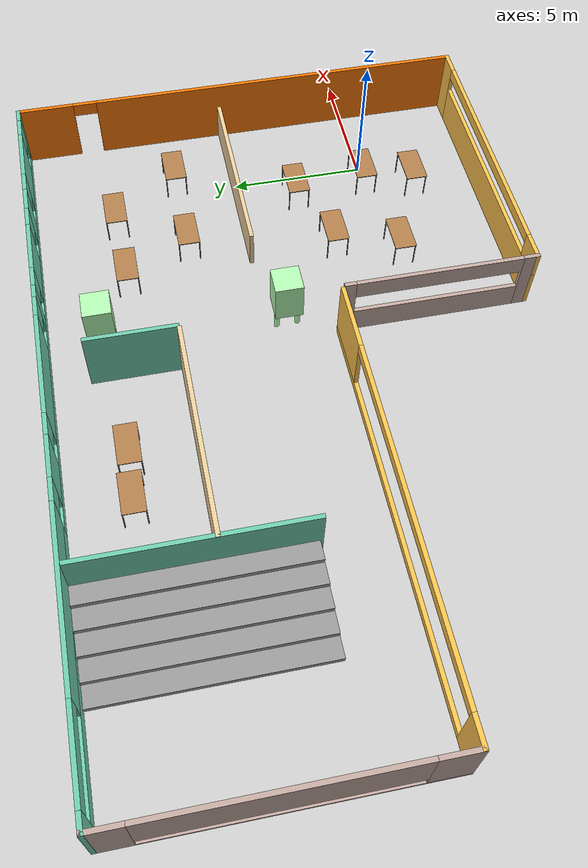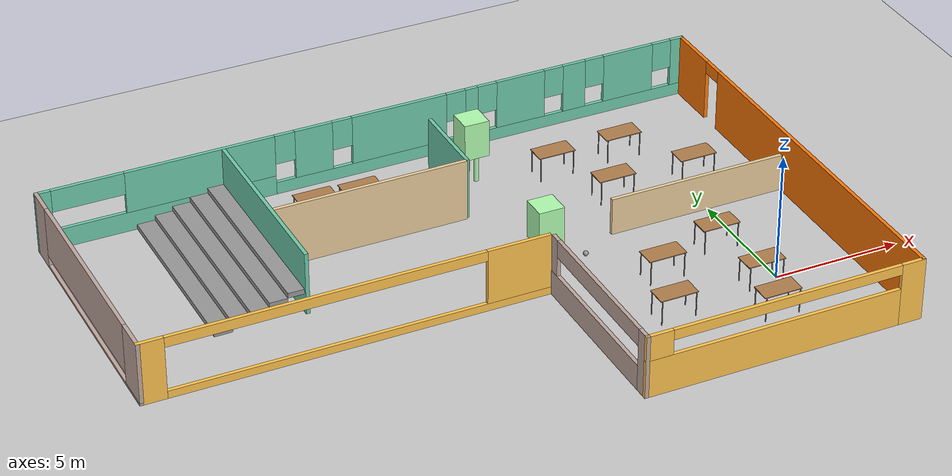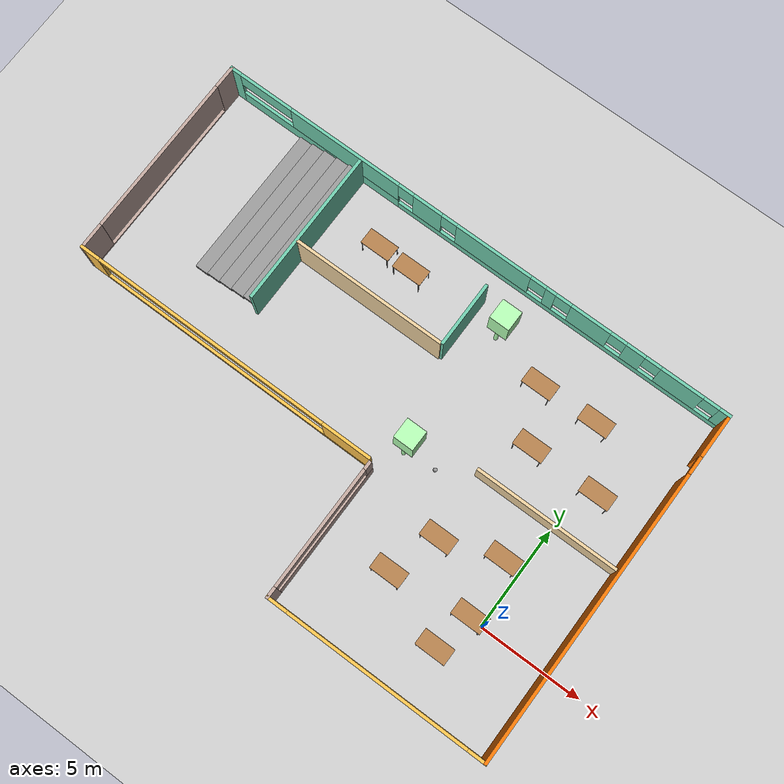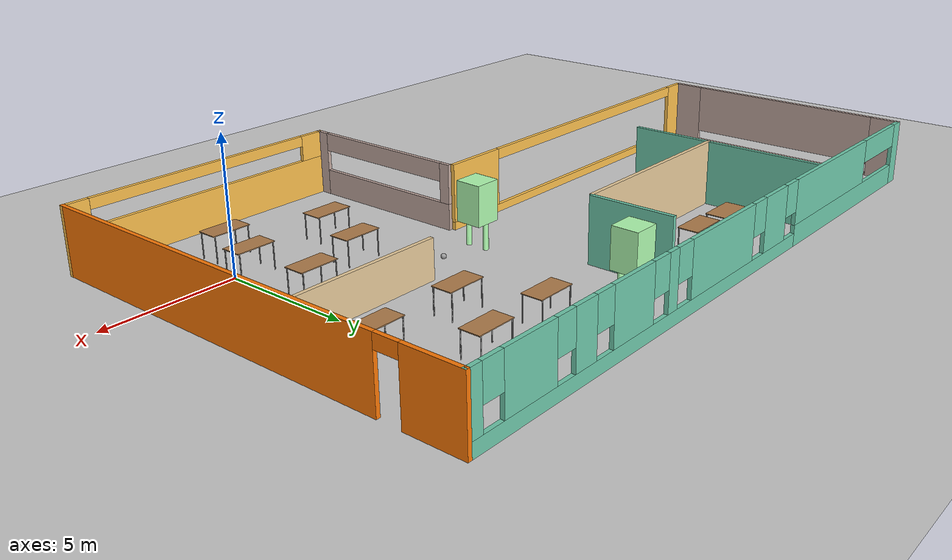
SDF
<sdf version="1.6">
 <world name="default">
  <light name="sun" type="directional">
   <pose>0 0 10 0 -0 0</pose>
   <diffuse>0.8 0.8 0.8 1</diffuse>
   <specular>0.2 0.2 0.2 1</specular>
   <attenuation>
    <range>1000</range>
    <constant>0.9</constant>
    <linear>0.01</linear>
    <quadratic>0.001</quadratic>
   </attenuation>
   <direction>-0.5 0.1 -0.9</direction>
  </light>
  <model name="ground_plane">
   <static>1</static>
   <link name="link">
    <collision name="collision">
     <geometry><plane><normal>0 0 1</normal><size>100 100</size></plane></geometry>
     <surface><friction><ode><mu>100</mu><mu2>50</mu2></ode></friction></surface>
    </collision>
    <visual name="visual">
     <cast_shadows>0</cast_shadows>
     <geometry><plane><normal>0 0 1</normal><size>100 100</size></plane></geometry>
     <material>
      <script><uri>file://media/materials/scripts/gazebo.material</uri><name>Gazebo/Grey</name></script>
     </material>
    </visual>
   </link>
  </model>
  <gravity>0 0 -9.8</gravity>
  <magnetic_field>6e-06 2.3e-05 -4.2e-05</magnetic_field>
  <atmosphere type="adiabatic"/>
  <physics name="default_physics" default="0" type="ode">
   <max_step_size>0.001</max_step_size>
   <real_time_factor>1</real_time_factor>
   <real_time_update_rate>1000</real_time_update_rate>
  </physics>
  <scene><ambient>0.4 0.4 0.4 1</ambient><background>0.7 0.7 0.7 1</background><shadows>1</shadows></scene>
  <spherical_coordinates>
   <surface_model>EARTH_WGS84</surface_model>
   <latitude_deg>0</latitude_deg>
   <longitude_deg>0</longitude_deg>
   <elevation>0</elevation>
   <heading_deg>0</heading_deg>
  </spherical_coordinates>
  <model name="MyOffice">
   <pose>-9.99386 4.31006 0 0 -0 0</pose>
   <link name="Stairs_1">
    <visual name="Stairs_1_Visual_0">
     <pose>-9.15396 4.81263 0.1 0 -0 1.5708</pose>
     <geometry><box><size>7.73533 0.7 0.2</size></box></geometry>
     <material>
      <script><uri>file://media/materials/scripts/gazebo.material</uri><name>Gazebo/Grey</name></script>
      <ambient>1 1 1 1</ambient>
     </material>
     <meta><layer>0</layer></meta>
    </visual>
    <collision name="Stairs_1_Collision_0">
     <geometry><box><size>7.73533 0.7 0.2</size></box></geometry>
     <pose>-9.15396 4.81263 0.1 0 -0 1.5708</pose>
    </collision>
    <visual name="Stairs_1_Visual_1">
     <pose>-8.45396 4.81263 0.3 0 -0 1.5708</pose>
     <geometry><box><size>7.73533 0.7 0.2</size></box></geometry>
     <material>
      <script><uri>file://media/materials/scripts/gazebo.material</uri><name>Gazebo/Grey</name></script>
      <ambient>1 1 1 1</ambient>
     </material>
     <meta><layer>0</layer></meta>
    </visual>
    <collision name="Stairs_1_Collision_1">
     <geometry><box><size>7.73533 0.7 0.2</size></box></geometry>
     <pose>-8.45396 4.81263 0.3 0 -0 1.5708</pose>
    </collision>
    <visual name="Stairs_1_Visual_2">
     <pose>-7.75396 4.81263 0.5 0 -0 1.5708</pose>
     <geometry><box><size>7.73533 0.7 0.2</size></box></geometry>
     <material>
      <script><uri>file://media/materials/scripts/gazebo.material</uri><name>Gazebo/Grey</name></script>
      <ambient>1 1 1 1</ambient>
     </material>
     <meta><layer>0</layer></meta>
    </visual>
    <collision name="Stairs_1_Collision_2">
     <geometry><box><size>7.73533 0.7 0.2</size></box></geometry>
     <pose>-7.75396 4.81263 0.5 0 -0 1.5708</pose>
    </collision>
    <visual name="Stairs_1_Visual_3">
     <pose>-7.05396 4.81263 0.7 0 -0 1.5708</pose>
     <geometry><box><size>7.73533 0.7 0.2</size></box></geometry>
     <material>
      <script><uri>file://media/materials/scripts/gazebo.material</uri><name>Gazebo/Grey</name></script>
      <ambient>1 1 1 1</ambient>
     </material>
     <meta><layer>0</layer></meta>
    </visual>
    <collision name="Stairs_1_Collision_3">
     <geometry><box><size>7.73533 0.7 0.2</size></box></geometry>
     <pose>-7.05396 4.81263 0.7 0 -0 1.5708</pose>
    </collision>
    <visual name="Stairs_1_Visual_4">
     <pose>-6.35396 4.81263 0.9 0 -0 1.5708</pose>
     <geometry><box><size>7.73533 0.7 0.2</size></box></geometry>
     <material>
      <script><uri>file://media/materials/scripts/gazebo.material</uri><name>Gazebo/Grey</name></script>
      <ambient>1 1 1 1</ambient>
     </material>
     <meta><layer>0</layer></meta>
    </visual>
    <collision name="Stairs_1_Collision_4">
     <geometry><box><size>7.73533 0.7 0.2</size></box></geometry>
     <pose>-6.35396 4.81263 0.9 0 -0 1.5708</pose>
    </collision>
   </link>
   <link name="Wall_1">
    <pose>-13.175 3.5 0 0 0 -1.5708</pose>
    <visual name="Wall_1_Visual_0">
     <pose>-4.66054 0 1.25 0 -0 0</pose>
     <geometry><box><size>1.17891 0.15 2.5</size></box></geometry>
     <material>
      <script><uri>file://media/materials/scripts/gazebo.material</uri><name>Gazebo/Grey</name></script>
      <ambient>0.760784 0.662745 0.627451 1</ambient>
     </material>
     <meta><layer>0</layer></meta>
    </visual>
    <collision name="Wall_1_Collision_0">
     <geometry><box><size>1.17891 0.15 2.5</size></box></geometry>
     <pose>-4.66054 0 1.25 0 -0 0</pose>
    </collision>
    <visual name="Wall_1_Visual_1">
     <pose>0.589456 0 0.05 0 -0 0</pose>
     <geometry><box><size>9.32109 0.15 0.1</size></box></geometry>
     <material>
      <script><uri>file://media/materials/scripts/gazebo.material</uri><name>Gazebo/Grey</name></script>
      <ambient>0.760784 0.662745 0.627451 1</ambient>
     </material>
     <meta><layer>0</layer></meta>
    </visual>
    <collision name="Wall_1_Collision_1">
     <geometry><box><size>9.32109 0.15 0.1</size></box></geometry>
     <pose>0.589456 0 0.05 0 -0 0</pose>
    </collision>
    <visual name="Wall_1_Visual_2">
     <pose>4.58946 0 1.3 0 -0 0</pose>
     <geometry><box><size>1.32109 0.15 2.4</size></box></geometry>
     <material>
      <script><uri>file://media/materials/scripts/gazebo.material</uri><name>Gazebo/Grey</name></script>
      <ambient>0.760784 0.662745 0.627451 1</ambient>
     </material>
     <meta><layer>0</layer></meta>
    </visual>
    <collision name="Wall_1_Collision_2">
     <geometry><box><size>1.32109 0.15 2.4</size></box></geometry>
     <pose>4.58946 0 1.3 0 -0 0</pose>
    </collision>
    <visual name="Wall_1_Visual_3">
     <pose>-0.071087 0 1.5 0 -0 0</pose>
     <geometry><box><size>8 0.15 2</size></box></geometry>
     <material>
      <script><uri>file://media/materials/scripts/gazebo.material</uri><name>Gazebo/Grey</name></script>
      <ambient>0.760784 0.662745 0.627451 1</ambient>
     </material>
     <meta><layer>0</layer></meta>
    </visual>
    <collision name="Wall_1_Collision_3">
     <geometry><box><size>8 0.15 2</size></box></geometry>
     <pose>-0.071087 0 1.5 0 -0 0</pose>
    </collision>
   </link>
   <link name="Wall_11">
    <collision name="Wall_11_Collision">
     <geometry><box><size>7.75 0.15 2.5</size></box></geometry>
     <pose>0 0 1.25 0 -0 0</pose>
    </collision>
    <visual name="Wall_11_Visual">
     <pose>0 0 1.25 0 -0 0</pose>
     <geometry><box><size>7.75 0.15 2.5</size></box></geometry>
     <material>
      <script><uri>file://media/materials/scripts/gazebo.material</uri><name>Gazebo/Grey</name></script>
      <ambient>0.921569 0.807843 0.615686 1</ambient>
     </material>
     <meta><layer>0</layer></meta>
    </visual>
    <pose>-2.18392 4.03899 0 0 -0 0</pose>
   </link>
   <link name="Wall_13">
    <collision name="Wall_13_Collision">
     <geometry><box><size>7.25 0.15 1.5</size></box></geometry>
     <pose>0 0 0.75 0 -0 0</pose>
    </collision>
    <visual name="Wall_13_Visual">
     <pose>0 0 0.75 0 -0 0</pose>
     <geometry><box><size>7.25 0.15 1.5</size></box></geometry>
     <material>
      <script><uri>file://media/materials/scripts/gazebo.material</uri><name>Gazebo/Grey</name></script>
      <ambient>0.921569 0.807843 0.615686 1</ambient>
     </material>
     <meta><layer>0</layer></meta>
    </visual>
    <pose>9.60987 0.795259 0 0 -0 3.14159</pose>
   </link>
   <link name="Wall_15">
    <collision name="Wall_15_Collision">
     <geometry><box><size>7.75 0.15 2.5</size></box></geometry>
     <pose>0 0 1.25 0 -0 0</pose>
    </collision>
    <visual name="Wall_15_Visual">
     <pose>0 0 1.25 0 -0 0</pose>
     <geometry><box><size>7.75 0.15 2.5</size></box></geometry>
     <material>
      <script><uri>file://media/materials/scripts/gazebo.material</uri><name>Gazebo/Grey</name></script>
      <ambient>0.435294 0.796078 0.67451 1</ambient>
     </material>
     <meta><layer>0</layer></meta>
    </visual>
    <pose>-5.9943 4.72008 0 0 0 -1.5708</pose>
   </link>
   <link name="Wall_17">
    <collision name="Wall_17_Collision">
     <geometry><box><size>3.25 0.15 2.5</size></box></geometry>
     <pose>0 0 1.25 0 -0 0</pose>
    </collision>
    <visual name="Wall_17_Visual">
     <pose>0 0 1.25 0 -0 0</pose>
     <geometry><box><size>3.25 0.15 2.5</size></box></geometry>
     <material>
      <script><uri>file://media/materials/scripts/gazebo.material</uri><name>Gazebo/Grey</name></script>
      <ambient>0.435294 0.796078 0.67451 1</ambient>
     </material>
     <meta><layer>0</layer></meta>
    </visual>
    <pose>1.73138 5.6554 0 0 -0 1.5708</pose>
   </link>
   <link name="Wall_2">
    <pose>-5.5 -1.675 0 0 -0 0</pose>
    <visual name="Wall_2_Visual_0">
     <pose>-7.24406 0 1.25 0 -0 0</pose>
     <geometry><box><size>1.01187 0.15 2.5</size></box></geometry>
     <material>
      <script><uri>file://media/materials/scripts/gazebo.material</uri><name>Gazebo/Grey</name></script>
      <ambient>1 0.764706 0.305882 1</ambient>
     </material>
     <meta><layer>0</layer></meta>
    </visual>
    <collision name="Wall_2_Collision_0">
     <geometry><box><size>1.01187 0.15 2.5</size></box></geometry>
     <pose>-7.24406 0 1.25 0 -0 0</pose>
    </collision>
    <visual name="Wall_2_Visual_1">
     <pose>0.505935 0 0.15 0 -0 0</pose>
     <geometry><box><size>14.4881 0.15 0.3</size></box></geometry>
     <material>
      <script><uri>file://media/materials/scripts/gazebo.material</uri><name>Gazebo/Grey</name></script>
      <ambient>1 0.764706 0.305882 1</ambient>
     </material>
     <meta><layer>0</layer></meta>
    </visual>
    <collision name="Wall_2_Collision_1">
     <geometry><box><size>14.4881 0.15 0.3</size></box></geometry>
     <pose>0.505935 0 0.15 0 -0 0</pose>
    </collision>
    <visual name="Wall_2_Visual_2">
     <pose>6.50594 0 1.4 0 -0 0</pose>
     <geometry><box><size>2.48813 0.15 2.2</size></box></geometry>
     <material>
      <script><uri>file://media/materials/scripts/gazebo.material</uri><name>Gazebo/Grey</name></script>
      <ambient>1 0.764706 0.305882 1</ambient>
     </material>
     <meta><layer>0</layer></meta>
    </visual>
    <collision name="Wall_2_Collision_2">
     <geometry><box><size>2.48813 0.15 2.2</size></box></geometry>
     <pose>6.50594 0 1.4 0 -0 0</pose>
    </collision>
    <visual name="Wall_2_Visual_3">
     <pose>-0.738131 0 2.3 0 -0 0</pose>
     <geometry><box><size>12 0.15 0.4</size></box></geometry>
     <material>
      <script><uri>file://media/materials/scripts/gazebo.material</uri><name>Gazebo/Grey</name></script>
      <ambient>1 0.764706 0.305882 1</ambient>
     </material>
     <meta><layer>0</layer></meta>
    </visual>
    <collision name="Wall_2_Collision_3">
     <geometry><box><size>12 0.15 0.4</size></box></geometry>
     <pose>-0.738131 0 2.3 0 -0 0</pose>
    </collision>
   </link>
   <link name="Wall_4">
    <pose>0 8.675 0 0 -0 0</pose>
    <visual name="Wall_4_Visual_0">
     <pose>-12.9493 0 1.25 0 -0 0</pose>
     <geometry><box><size>0.601453 0.15 2.5</size></box></geometry>
     <material>
      <script><uri>file://media/materials/scripts/gazebo.material</uri><name>Gazebo/Grey</name></script>
      <ambient>0.435294 0.796078 0.67451 1</ambient>
     </material>
     <meta><layer>0</layer></meta>
    </visual>
    <collision name="Wall_4_Collision_0">
     <geometry><box><size>0.601453 0.15 2.5</size></box></geometry>
     <pose>-12.9493 0 1.25 0 -0 0</pose>
    </collision>
    <visual name="Wall_4_Visual_1">
     <pose>-8.30819 0 0.4 0 -0 0</pose>
     <geometry><box><size>8.68071 0.15 0.8</size></box></geometry>
     <material>
      <script><uri>file://media/materials/scripts/gazebo.material</uri><name>Gazebo/Grey</name></script>
      <ambient>0.435294 0.796078 0.67451 1</ambient>
     </material>
     <meta><layer>0</layer></meta>
    </visual>
    <collision name="Wall_4_Collision_1">
     <geometry><box><size>8.68071 0.15 0.8</size></box></geometry>
     <pose>-8.30819 0 0.4 0 -0 0</pose>
    </collision>
    <visual name="Wall_4_Visual_2">
     <pose>4.64108 0 0.25 0 -0 0</pose>
     <geometry><box><size>17.2178 0.15 0.5</size></box></geometry>
     <material>
      <script><uri>file://media/materials/scripts/gazebo.material</uri><name>Gazebo/Grey</name></script>
      <ambient>0.435294 0.796078 0.67451 1</ambient>
     </material>
     <meta><layer>0</layer></meta>
    </visual>
    <collision name="Wall_4_Collision_2">
     <geometry><box><size>17.2178 0.15 0.5</size></box></geometry>
     <pose>4.64108 0 0.25 0 -0 0</pose>
    </collision>
    <visual name="Wall_4_Visual_3">
     <pose>-2.41009 0 1.5 0 -0 0</pose>
     <geometry><box><size>1.51549 0.15 2</size></box></geometry>
     <material>
      <script><uri>file://media/materials/scripts/gazebo.material</uri><name>Gazebo/Grey</name></script>
      <ambient>0.435294 0.796078 0.67451 1</ambient>
     </material>
     <meta><layer>0</layer></meta>
    </visual>
    <collision name="Wall_4_Collision_3">
     <geometry><box><size>1.51549 0.15 2</size></box></geometry>
     <pose>-2.41009 0 1.5 0 -0 0</pose>
    </collision>
    <visual name="Wall_4_Visual_4">
     <pose>1.09786 0 1.5 0 -0 0</pose>
     <geometry><box><size>3.90042 0.15 2</size></box></geometry>
     <material>
      <script><uri>file://media/materials/scripts/gazebo.material</uri><name>Gazebo/Grey</name></script>
      <ambient>0.435294 0.796078 0.67451 1</ambient>
     </material>
     <meta><layer>0</layer></meta>
    </visual>
    <collision name="Wall_4_Collision_4">
     <geometry><box><size>3.90042 0.15 2</size></box></geometry>
     <pose>1.09786 0 1.5 0 -0 0</pose>
    </collision>
    <visual name="Wall_4_Visual_5">
     <pose>4.10318 0 1.5 0 -0 0</pose>
     <geometry><box><size>0.510201 0.15 2</size></box></geometry>
     <material>
      <script><uri>file://media/materials/scripts/gazebo.material</uri><name>Gazebo/Grey</name></script>
      <ambient>0.435294 0.796078 0.67451 1</ambient>
     </material>
     <meta><layer>0</layer></meta>
    </visual>
    <collision name="Wall_4_Collision_5">
     <geometry><box><size>0.510201 0.15 2</size></box></geometry>
     <pose>4.10318 0 1.5 0 -0 0</pose>
    </collision>
    <visual name="Wall_4_Visual_6">
     <pose>6.17414 0 1.5 0 -0 0</pose>
     <geometry><box><size>2.03172 0.15 2</size></box></geometry>
     <material>
      <script><uri>file://media/materials/scripts/gazebo.material</uri><name>Gazebo/Grey</name></script>
      <ambient>0.435294 0.796078 0.67451 1</ambient>
     </material>
     <meta><layer>0</layer></meta>
    </visual>
    <collision name="Wall_4_Collision_6">
     <geometry><box><size>2.03172 0.15 2</size></box></geometry>
     <pose>6.17414 0 1.5 0 -0 0</pose>
    </collision>
    <visual name="Wall_4_Visual_7">
     <pose>8.46963 0 1.5 0 -0 0</pose>
     <geometry><box><size>0.959263 0.15 2</size></box></geometry>
     <material>
      <script><uri>file://media/materials/scripts/gazebo.material</uri><name>Gazebo/Grey</name></script>
      <ambient>0.435294 0.796078 0.67451 1</ambient>
     </material>
     <meta><layer>0</layer></meta>
    </visual>
    <collision name="Wall_4_Collision_7">
     <geometry><box><size>0.959263 0.15 2</size></box></geometry>
     <pose>8.46963 0 1.5 0 -0 0</pose>
    </collision>
    <visual name="Wall_4_Visual_8">
     <pose>10.8153 0 1.5 0 -0 0</pose>
     <geometry><box><size>2.1321 0.15 2</size></box></geometry>
     <material>
      <script><uri>file://media/materials/scripts/gazebo.material</uri><name>Gazebo/Grey</name></script>
      <ambient>0.435294 0.796078 0.67451 1</ambient>
     </material>
     <meta><layer>0</layer></meta>
    </visual>
    <collision name="Wall_4_Collision_8">
     <geometry><box><size>2.1321 0.15 2</size></box></geometry>
     <pose>10.8153 0 1.5 0 -0 0</pose>
    </collision>
    <visual name="Wall_4_Visual_9">
     <pose>12.9657 0 1.5 0 -0 0</pose>
     <geometry><box><size>0.568637 0.15 2</size></box></geometry>
     <material>
      <script><uri>file://media/materials/scripts/gazebo.material</uri><name>Gazebo/Grey</name></script>
      <ambient>0.435294 0.796078 0.67451 1</ambient>
     </material>
     <meta><layer>0</layer></meta>
    </visual>
    <collision name="Wall_4_Collision_9">
     <geometry><box><size>0.568637 0.15 2</size></box></geometry>
     <pose>12.9657 0 1.5 0 -0 0</pose>
    </collision>
    <visual name="Wall_4_Visual_10">
     <pose>-6.90819 0 1.65 0 -0 0</pose>
     <geometry><box><size>5.88071 0.15 1.7</size></box></geometry>
     <material>
      <script><uri>file://media/materials/scripts/gazebo.material</uri><name>Gazebo/Grey</name></script>
      <ambient>0.435294 0.796078 0.67451 1</ambient>
     </material>
     <meta><layer>0</layer></meta>
    </visual>
    <collision name="Wall_4_Collision_10">
     <geometry><box><size>5.88071 0.15 1.7</size></box></geometry>
     <pose>-6.90819 0 1.65 0 -0 0</pose>
    </collision>
    <visual name="Wall_4_Visual_11">
     <pose>-1.25235 0 1.9 0 -0 0</pose>
     <geometry><box><size>0.8 0.15 1.2</size></box></geometry>
     <material>
      <script><uri>file://media/materials/scripts/gazebo.material</uri><name>Gazebo/Grey</name></script>
      <ambient>0.435294 0.796078 0.67451 1</ambient>
     </material>
     <meta><layer>0</layer></meta>
    </visual>
    <collision name="Wall_4_Collision_11">
     <geometry><box><size>0.8 0.15 1.2</size></box></geometry>
     <pose>-1.25235 0 1.9 0 -0 0</pose>
    </collision>
    <visual name="Wall_4_Visual_12">
     <pose>3.44807 0 1.9 0 -0 0</pose>
     <geometry><box><size>0.8 0.15 1.2</size></box></geometry>
     <material>
      <script><uri>file://media/materials/scripts/gazebo.material</uri><name>Gazebo/Grey</name></script>
      <ambient>0.435294 0.796078 0.67451 1</ambient>
     </material>
     <meta><layer>0</layer></meta>
    </visual>
    <collision name="Wall_4_Collision_12">
     <geometry><box><size>0.8 0.15 1.2</size></box></geometry>
     <pose>3.44807 0 1.9 0 -0 0</pose>
    </collision>
    <visual name="Wall_4_Visual_13">
     <pose>4.75828 0 1.9 0 -0 0</pose>
     <geometry><box><size>0.8 0.15 1.2</size></box></geometry>
     <material>
      <script><uri>file://media/materials/scripts/gazebo.material</uri><name>Gazebo/Grey</name></script>
      <ambient>0.435294 0.796078 0.67451 1</ambient>
     </material>
     <meta><layer>0</layer></meta>
    </visual>
    <collision name="Wall_4_Collision_13">
     <geometry><box><size>0.8 0.15 1.2</size></box></geometry>
     <pose>4.75828 0 1.9 0 -0 0</pose>
    </collision>
    <visual name="Wall_4_Visual_14">
     <pose>7.59 0 1.9 0 -0 0</pose>
     <geometry><box><size>0.8 0.15 1.2</size></box></geometry>
     <material>
      <script><uri>file://media/materials/scripts/gazebo.material</uri><name>Gazebo/Grey</name></script>
      <ambient>0.435294 0.796078 0.67451 1</ambient>
     </material>
     <meta><layer>0</layer></meta>
    </visual>
    <collision name="Wall_4_Collision_14">
     <geometry><box><size>0.8 0.15 1.2</size></box></geometry>
     <pose>7.59 0 1.9 0 -0 0</pose>
    </collision>
    <visual name="Wall_4_Visual_15">
     <pose>9.34926 0 1.9 0 -0 0</pose>
     <geometry><box><size>0.8 0.15 1.2</size></box></geometry>
     <material>
      <script><uri>file://media/materials/scripts/gazebo.material</uri><name>Gazebo/Grey</name></script>
      <ambient>0.435294 0.796078 0.67451 1</ambient>
     </material>
     <meta><layer>0</layer></meta>
    </visual>
    <collision name="Wall_4_Collision_15">
     <geometry><box><size>0.8 0.15 1.2</size></box></geometry>
     <pose>9.34926 0 1.9 0 -0 0</pose>
    </collision>
    <visual name="Wall_4_Visual_16">
     <pose>12.2814 0 1.9 0 -0 0</pose>
     <geometry><box><size>0.8 0.15 1.2</size></box></geometry>
     <material>
      <script><uri>file://media/materials/scripts/gazebo.material</uri><name>Gazebo/Grey</name></script>
      <ambient>0.435294 0.796078 0.67451 1</ambient>
     </material>
     <meta><layer>0</layer></meta>
    </visual>
    <collision name="Wall_4_Collision_16">
     <geometry><box><size>0.8 0.15 1.2</size></box></geometry>
     <pose>12.2814 0 1.9 0 -0 0</pose>
    </collision>
    <visual name="Wall_4_Visual_17">
     <pose>-3.56784 0 1.9 0 -0 0</pose>
     <geometry><box><size>0.8 0.15 1.2</size></box></geometry>
     <material>
      <script><uri>file://media/materials/scripts/gazebo.material</uri><name>Gazebo/Grey</name></script>
      <ambient>0.435294 0.796078 0.67451 1</ambient>
     </material>
     <meta><layer>0</layer></meta>
    </visual>
    <collision name="Wall_4_Collision_17">
     <geometry><box><size>0.8 0.15 1.2</size></box></geometry>
     <pose>-3.56784 0 1.9 0 -0 0</pose>
    </collision>
    <visual name="Wall_4_Visual_18">
     <pose>-11.2485 0 2.05 0 -0 0</pose>
     <geometry><box><size>2.8 0.15 0.9</size></box></geometry>
     <material>
      <script><uri>file://media/materials/scripts/gazebo.material</uri><name>Gazebo/Grey</name></script>
      <ambient>0.435294 0.796078 0.67451 1</ambient>
     </material>
     <meta><layer>0</layer></meta>
    </visual>
    <collision name="Wall_4_Collision_18">
     <geometry><box><size>2.8 0.15 0.9</size></box></geometry>
     <pose>-11.2485 0 2.05 0 -0 0</pose>
    </collision>
   </link>
   <link name="Wall_5">
    <pose>13.175 0 0 0 0 -1.5708</pose>
    <visual name="Wall_5_Visual_0">
     <pose>-7.64597 0 1.25 0 -0 0</pose>
     <geometry><box><size>2.20807 0.15 2.5</size></box></geometry>
     <material>
      <script><uri>file://media/materials/scripts/gazebo.material</uri><name>Gazebo/Grey</name></script>
      <ambient>0.996078 0.47451 0.0196078 1</ambient>
     </material>
     <meta><layer>0</layer></meta>
    </visual>
    <collision name="Wall_5_Collision_0">
     <geometry><box><size>2.20807 0.15 2.5</size></box></geometry>
     <pose>-7.64597 0 1.25 0 -0 0</pose>
    </collision>
    <visual name="Wall_5_Visual_1">
     <pose>1.55403 0 1.25 0 -0 0</pose>
     <geometry><box><size>14.3919 0.15 2.5</size></box></geometry>
     <material>
      <script><uri>file://media/materials/scripts/gazebo.material</uri><name>Gazebo/Grey</name></script>
      <ambient>0.996078 0.47451 0.0196078 1</ambient>
     </material>
     <meta><layer>0</layer></meta>
    </visual>
    <collision name="Wall_5_Collision_1">
     <geometry><box><size>14.3919 0.15 2.5</size></box></geometry>
     <pose>1.55403 0 1.25 0 -0 0</pose>
    </collision>
    <visual name="Wall_5_Visual_2">
     <pose>-6.09193 0 2.25 0 -0 0</pose>
     <geometry><box><size>0.9 0.15 0.5</size></box></geometry>
     <material>
      <script><uri>file://media/materials/scripts/gazebo.material</uri><name>Gazebo/Grey</name></script>
      <ambient>0.996078 0.47451 0.0196078 1</ambient>
     </material>
     <meta><layer>0</layer></meta>
    </visual>
    <collision name="Wall_5_Collision_2">
     <geometry><box><size>0.9 0.15 0.5</size></box></geometry>
     <pose>-6.09193 0 2.25 0 -0 0</pose>
    </collision>
   </link>
   <link name="Wall_7">
    <pose>7.75 -8.675 0 0 -0 3.14159</pose>
    <visual name="Wall_7_Visual_0">
     <pose>-5.02514 0 1.25 0 -0 0</pose>
     <geometry><box><size>0.949727 0.15 2.5</size></box></geometry>
     <material>
      <script><uri>file://media/materials/scripts/gazebo.material</uri><name>Gazebo/Grey</name></script>
      <ambient>1 0.764706 0.305882 1</ambient>
     </material>
     <meta><layer>0</layer></meta>
    </visual>
    <collision name="Wall_7_Collision_0">
     <geometry><box><size>0.949727 0.15 2.5</size></box></geometry>
     <pose>-5.02514 0 1.25 0 -0 0</pose>
    </collision>
    <visual name="Wall_7_Visual_1">
     <pose>0.474864 0 0.75 0 -0 0</pose>
     <geometry><box><size>10.0503 0.15 1.5</size></box></geometry>
     <material>
      <script><uri>file://media/materials/scripts/gazebo.material</uri><name>Gazebo/Grey</name></script>
      <ambient>1 0.764706 0.305882 1</ambient>
     </material>
     <meta><layer>0</layer></meta>
    </visual>
    <collision name="Wall_7_Collision_1">
     <geometry><box><size>10.0503 0.15 1.5</size></box></geometry>
     <pose>0.474864 0 0.75 0 -0 0</pose>
    </collision>
    <visual name="Wall_7_Visual_2">
     <pose>4.97486 0 2 0 -0 0</pose>
     <geometry><box><size>1.05027 0.15 1</size></box></geometry>
     <material>
      <script><uri>file://media/materials/scripts/gazebo.material</uri><name>Gazebo/Grey</name></script>
      <ambient>1 0.764706 0.305882 1</ambient>
     </material>
     <meta><layer>0</layer></meta>
    </visual>
    <collision name="Wall_7_Collision_2">
     <geometry><box><size>1.05027 0.15 1</size></box></geometry>
     <pose>4.97486 0 2 0 -0 0</pose>
    </collision>
    <visual name="Wall_7_Visual_3">
     <pose>-0.050273 0 2.3 0 -0 0</pose>
     <geometry><box><size>9 0.15 0.4</size></box></geometry>
     <material>
      <script><uri>file://media/materials/scripts/gazebo.material</uri><name>Gazebo/Grey</name></script>
      <ambient>1 0.764706 0.305882 1</ambient>
     </material>
     <meta><layer>0</layer></meta>
    </visual>
    <collision name="Wall_7_Collision_3">
     <geometry><box><size>9 0.15 0.4</size></box></geometry>
     <pose>-0.050273 0 2.3 0 -0 0</pose>
    </collision>
   </link>
   <link name="Wall_8">
    <pose>2.325 -5.25 0 0 -0 1.5708</pose>
    <visual name="Wall_8_Visual_0">
     <pose>-3.21189 0 1.25 0 -0 0</pose>
     <geometry><box><size>0.576225 0.15 2.5</size></box></geometry>
     <material>
      <script><uri>file://media/materials/scripts/gazebo.material</uri><name>Gazebo/Grey</name></script>
      <ambient>0.760784 0.662745 0.627451 1</ambient>
     </material>
     <meta><layer>0</layer></meta>
    </visual>
    <collision name="Wall_8_Collision_0">
     <geometry><box><size>0.576225 0.15 2.5</size></box></geometry>
     <pose>-3.21189 0 1.25 0 -0 0</pose>
    </collision>
    <visual name="Wall_8_Visual_1">
     <pose>0.288113 0 0.5 0 -0 0</pose>
     <geometry><box><size>6.42378 0.15 1</size></box></geometry>
     <material>
      <script><uri>file://media/materials/scripts/gazebo.material</uri><name>Gazebo/Grey</name></script>
      <ambient>0.760784 0.662745 0.627451 1</ambient>
     </material>
     <meta><layer>0</layer></meta>
    </visual>
    <collision name="Wall_8_Collision_1">
     <geometry><box><size>6.42378 0.15 1</size></box></geometry>
     <pose>0.288113 0 0.5 0 -0 0</pose>
    </collision>
    <visual name="Wall_8_Visual_2">
     <pose>3.28811 0 1.75 0 -0 0</pose>
     <geometry><box><size>0.423775 0.15 1.5</size></box></geometry>
     <material>
      <script><uri>file://media/materials/scripts/gazebo.material</uri><name>Gazebo/Grey</name></script>
      <ambient>0.760784 0.662745 0.627451 1</ambient>
     </material>
     <meta><layer>0</layer></meta>
    </visual>
    <collision name="Wall_8_Collision_2">
     <geometry><box><size>0.423775 0.15 1.5</size></box></geometry>
     <pose>3.28811 0 1.75 0 -0 0</pose>
    </collision>
    <visual name="Wall_8_Visual_3">
     <pose>0.076225 0 2.15 0 -0 0</pose>
     <geometry><box><size>6 0.15 0.7</size></box></geometry>
     <material>
      <script><uri>file://media/materials/scripts/gazebo.material</uri><name>Gazebo/Grey</name></script>
      <ambient>0.760784 0.662745 0.627451 1</ambient>
     </material>
     <meta><layer>0</layer></meta>
    </visual>
    <collision name="Wall_8_Collision_3">
     <geometry><box><size>6 0.15 0.7</size></box></geometry>
     <pose>0.076225 0 2.15 0 -0 0</pose>
    </collision>
   </link>
   <static>1</static>
  </model>
  <model name="table">
   <static>1</static>
   <link name="link">
    <collision name="surface">
     <pose>0 0 1 0 -0 0</pose>
     <geometry><box><size>1.5 0.8 0.03</size></box></geometry>
     <surface><friction><ode><mu>0.6</mu><mu2>0.6</mu2></ode></friction></surface>
    </collision>
    <visual name="visual1">
     <pose>0 0 1 0 -0 0</pose>
     <geometry><box><size>1.5 0.8 0.03</size></box></geometry>
     <material>
      <script><uri>file://media/materials/scripts/gazebo.material</uri><name>Gazebo/Wood</name></script>
     </material>
    </visual>
    <collision name="front_left_leg">
     <pose>0.68 0.38 0.5 0 -0 0</pose>
     <geometry><cylinder><radius>0.02</radius><length>1</length></cylinder></geometry>
    </collision>
    <visual name="front_left_leg">
     <pose>0.68 0.38 0.5 0 -0 0</pose>
     <geometry><cylinder><radius>0.02</radius><length>1</length></cylinder></geometry>
     <material>
      <script><uri>file://media/materials/scripts/gazebo.material</uri><name>Gazebo/Grey</name></script>
     </material>
    </visual>
    <collision name="front_right_leg">
     <pose>0.68 -0.38 0.5 0 -0 0</pose>
     <geometry><cylinder><radius>0.02</radius><length>1</length></cylinder></geometry>
    </collision>
    <visual name="front_right_leg">
     <pose>0.68 -0.38 0.5 0 -0 0</pose>
     <geometry><cylinder><radius>0.02</radius><length>1</length></cylinder></geometry>
     <material>
      <script><uri>file://media/materials/scripts/gazebo.material</uri><name>Gazebo/Grey</name></script>
     </material>
    </visual>
    <collision name="back_right_leg">
     <pose>-0.68 -0.38 0.5 0 -0 0</pose>
     <geometry><cylinder><radius>0.02</radius><length>1</length></cylinder></geometry>
    </collision>
    <visual name="back_right_leg">
     <pose>-0.68 -0.38 0.5 0 -0 0</pose>
     <geometry><cylinder><radius>0.02</radius><length>1</length></cylinder></geometry>
     <material>
      <script><uri>file://media/materials/scripts/gazebo.material</uri><name>Gazebo/Grey</name></script>
     </material>
    </visual>
    <collision name="back_left_leg">
     <pose>-0.68 0.38 0.5 0 -0 0</pose>
     <geometry><cylinder><radius>0.02</radius><length>1</length></cylinder></geometry>
    </collision>
    <visual name="back_left_leg">
     <pose>-0.68 0.38 0.5 0 -0 0</pose>
     <geometry><cylinder><radius>0.02</radius><length>1</length></cylinder></geometry>
     <material>
      <script><uri>file://media/materials/scripts/gazebo.material</uri><name>Gazebo/Grey</name></script>
     </material>
    </visual>
   </link>
   <pose>-4.01505 9.79336 0 0 -0 0</pose>
  </model>
  <model name="table_0">
   <static>1</static>
   <link name="link">
    <collision name="surface">
     <pose>0 0 1 0 -0 0</pose>
     <geometry><box><size>1.5 0.8 0.03</size></box></geometry>
     <surface><friction><ode><mu>0.6</mu><mu2>0.6</mu2></ode></friction></surface>
    </collision>
    <visual name="visual1">
     <pose>0 0 1 0 -0 0</pose>
     <geometry><box><size>1.5 0.8 0.03</size></box></geometry>
     <material>
      <script><uri>file://media/materials/scripts/gazebo.material</uri><name>Gazebo/Wood</name></script>
     </material>
    </visual>
    <collision name="front_left_leg">
     <pose>0.68 0.38 0.5 0 -0 0</pose>
     <geometry><cylinder><radius>0.02</radius><length>1</length></cylinder></geometry>
    </collision>
    <visual name="front_left_leg">
     <pose>0.68 0.38 0.5 0 -0 0</pose>
     <geometry><cylinder><radius>0.02</radius><length>1</length></cylinder></geometry>
     <material>
      <script><uri>file://media/materials/scripts/gazebo.material</uri><name>Gazebo/Grey</name></script>
     </material>
    </visual>
    <collision name="front_right_leg">
     <pose>0.68 -0.38 0.5 0 -0 0</pose>
     <geometry><cylinder><radius>0.02</radius><length>1</length></cylinder></geometry>
    </collision>
    <visual name="front_right_leg">
     <pose>0.68 -0.38 0.5 0 -0 0</pose>
     <geometry><cylinder><radius>0.02</radius><length>1</length></cylinder></geometry>
     <material>
      <script><uri>file://media/materials/scripts/gazebo.material</uri><name>Gazebo/Grey</name></script>
     </material>
    </visual>
    <collision name="back_right_leg">
     <pose>-0.68 -0.38 0.5 0 -0 0</pose>
     <geometry><cylinder><radius>0.02</radius><length>1</length></cylinder></geometry>
    </collision>
    <visual name="back_right_leg">
     <pose>-0.68 -0.38 0.5 0 -0 0</pose>
     <geometry><cylinder><radius>0.02</radius><length>1</length></cylinder></geometry>
     <material>
      <script><uri>file://media/materials/scripts/gazebo.material</uri><name>Gazebo/Grey</name></script>
     </material>
    </visual>
    <collision name="back_left_leg">
     <pose>-0.68 0.38 0.5 0 -0 0</pose>
     <geometry><cylinder><radius>0.02</radius><length>1</length></cylinder></geometry>
    </collision>
    <visual name="back_left_leg">
     <pose>-0.68 0.38 0.5 0 -0 0</pose>
     <geometry><cylinder><radius>0.02</radius><length>1</length></cylinder></geometry>
     <material>
      <script><uri>file://media/materials/scripts/gazebo.material</uri><name>Gazebo/Grey</name></script>
     </material>
    </visual>
   </link>
   <pose>-1.14688 9.87615 0 0 -0 0</pose>
  </model>
  <model name="table_1">
   <static>1</static>
   <link name="link">
    <collision name="surface">
     <pose>0 0 1 0 -0 0</pose>
     <geometry><box><size>1.5 0.8 0.03</size></box></geometry>
     <surface><friction><ode><mu>0.6</mu><mu2>0.6</mu2></ode></friction></surface>
    </collision>
    <visual name="visual1">
     <pose>0 0 1 0 -0 0</pose>
     <geometry><box><size>1.5 0.8 0.03</size></box></geometry>
     <material>
      <script><uri>file://media/materials/scripts/gazebo.material</uri><name>Gazebo/Wood</name></script>
     </material>
    </visual>
    <collision name="front_left_leg">
     <pose>0.68 0.38 0.5 0 -0 0</pose>
     <geometry><cylinder><radius>0.02</radius><length>1</length></cylinder></geometry>
    </collision>
    <visual name="front_left_leg">
     <pose>0.68 0.38 0.5 0 -0 0</pose>
     <geometry><cylinder><radius>0.02</radius><length>1</length></cylinder></geometry>
     <material>
      <script><uri>file://media/materials/scripts/gazebo.material</uri><name>Gazebo/Grey</name></script>
     </material>
    </visual>
    <collision name="front_right_leg">
     <pose>0.68 -0.38 0.5 0 -0 0</pose>
     <geometry><cylinder><radius>0.02</radius><length>1</length></cylinder></geometry>
    </collision>
    <visual name="front_right_leg">
     <pose>0.68 -0.38 0.5 0 -0 0</pose>
     <geometry><cylinder><radius>0.02</radius><length>1</length></cylinder></geometry>
     <material>
      <script><uri>file://media/materials/scripts/gazebo.material</uri><name>Gazebo/Grey</name></script>
     </material>
    </visual>
    <collision name="back_right_leg">
     <pose>-0.68 -0.38 0.5 0 -0 0</pose>
     <geometry><cylinder><radius>0.02</radius><length>1</length></cylinder></geometry>
    </collision>
    <visual name="back_right_leg">
     <pose>-0.68 -0.38 0.5 0 -0 0</pose>
     <geometry><cylinder><radius>0.02</radius><length>1</length></cylinder></geometry>
     <material>
      <script><uri>file://media/materials/scripts/gazebo.material</uri><name>Gazebo/Grey</name></script>
     </material>
    </visual>
    <collision name="back_left_leg">
     <pose>-0.68 0.38 0.5 0 -0 0</pose>
     <geometry><cylinder><radius>0.02</radius><length>1</length></cylinder></geometry>
    </collision>
    <visual name="back_left_leg">
     <pose>-0.68 0.38 0.5 0 -0 0</pose>
     <geometry><cylinder><radius>0.02</radius><length>1</length></cylinder></geometry>
     <material>
      <script><uri>file://media/materials/scripts/gazebo.material</uri><name>Gazebo/Grey</name></script>
     </material>
    </visual>
   </link>
   <pose>-2.73953 7.35385 0 0 -0 0</pose>
  </model>
  <model name="table_2">
   <static>1</static>
   <link name="link">
    <collision name="surface">
     <pose>0 0 1 0 -0 0</pose>
     <geometry><box><size>1.5 0.8 0.03</size></box></geometry>
     <surface><friction><ode><mu>0.6</mu><mu2>0.6</mu2></ode></friction></surface>
    </collision>
    <visual name="visual1">
     <pose>0 0 1 0 -0 0</pose>
     <geometry><box><size>1.5 0.8 0.03</size></box></geometry>
     <material>
      <script><uri>file://media/materials/scripts/gazebo.material</uri><name>Gazebo/Wood</name></script>
     </material>
    </visual>
    <collision name="front_left_leg">
     <pose>0.68 0.38 0.5 0 -0 0</pose>
     <geometry><cylinder><radius>0.02</radius><length>1</length></cylinder></geometry>
    </collision>
    <visual name="front_left_leg">
     <pose>0.68 0.38 0.5 0 -0 0</pose>
     <geometry><cylinder><radius>0.02</radius><length>1</length></cylinder></geometry>
     <material>
      <script><uri>file://media/materials/scripts/gazebo.material</uri><name>Gazebo/Grey</name></script>
     </material>
    </visual>
    <collision name="front_right_leg">
     <pose>0.68 -0.38 0.5 0 -0 0</pose>
     <geometry><cylinder><radius>0.02</radius><length>1</length></cylinder></geometry>
    </collision>
    <visual name="front_right_leg">
     <pose>0.68 -0.38 0.5 0 -0 0</pose>
     <geometry><cylinder><radius>0.02</radius><length>1</length></cylinder></geometry>
     <material>
      <script><uri>file://media/materials/scripts/gazebo.material</uri><name>Gazebo/Grey</name></script>
     </material>
    </visual>
    <collision name="back_right_leg">
     <pose>-0.68 -0.38 0.5 0 -0 0</pose>
     <geometry><cylinder><radius>0.02</radius><length>1</length></cylinder></geometry>
    </collision>
    <visual name="back_right_leg">
     <pose>-0.68 -0.38 0.5 0 -0 0</pose>
     <geometry><cylinder><radius>0.02</radius><length>1</length></cylinder></geometry>
     <material>
      <script><uri>file://media/materials/scripts/gazebo.material</uri><name>Gazebo/Grey</name></script>
     </material>
    </visual>
    <collision name="back_left_leg">
     <pose>-0.68 0.38 0.5 0 -0 0</pose>
     <geometry><cylinder><radius>0.02</radius><length>1</length></cylinder></geometry>
    </collision>
    <visual name="back_left_leg">
     <pose>-0.68 0.38 0.5 0 -0 0</pose>
     <geometry><cylinder><radius>0.02</radius><length>1</length></cylinder></geometry>
     <material>
      <script><uri>file://media/materials/scripts/gazebo.material</uri><name>Gazebo/Grey</name></script>
     </material>
    </visual>
   </link>
   <pose>0.676535 7.34865 0 0 -0 0</pose>
  </model>
  <model name="table_3">
   <static>1</static>
   <link name="link">
    <collision name="surface">
     <pose>0 0 1 0 -0 0</pose>
     <geometry><box><size>1.5 0.8 0.03</size></box></geometry>
     <surface><friction><ode><mu>0.6</mu><mu2>0.6</mu2></ode></friction></surface>
    </collision>
    <visual name="visual1">
     <pose>0 0 1 0 -0 0</pose>
     <geometry><box><size>1.5 0.8 0.03</size></box></geometry>
     <material>
      <script><uri>file://media/materials/scripts/gazebo.material</uri><name>Gazebo/Wood</name></script>
     </material>
    </visual>
    <collision name="front_left_leg">
     <pose>0.68 0.38 0.5 0 -0 0</pose>
     <geometry><cylinder><radius>0.02</radius><length>1</length></cylinder></geometry>
    </collision>
    <visual name="front_left_leg">
     <pose>0.68 0.38 0.5 0 -0 0</pose>
     <geometry><cylinder><radius>0.02</radius><length>1</length></cylinder></geometry>
     <material>
      <script><uri>file://media/materials/scripts/gazebo.material</uri><name>Gazebo/Grey</name></script>
     </material>
    </visual>
    <collision name="front_right_leg">
     <pose>0.68 -0.38 0.5 0 -0 0</pose>
     <geometry><cylinder><radius>0.02</radius><length>1</length></cylinder></geometry>
    </collision>
    <visual name="front_right_leg">
     <pose>0.68 -0.38 0.5 0 -0 0</pose>
     <geometry><cylinder><radius>0.02</radius><length>1</length></cylinder></geometry>
     <material>
      <script><uri>file://media/materials/scripts/gazebo.material</uri><name>Gazebo/Grey</name></script>
     </material>
    </visual>
    <collision name="back_right_leg">
     <pose>-0.68 -0.38 0.5 0 -0 0</pose>
     <geometry><cylinder><radius>0.02</radius><length>1</length></cylinder></geometry>
    </collision>
    <visual name="back_right_leg">
     <pose>-0.68 -0.38 0.5 0 -0 0</pose>
     <geometry><cylinder><radius>0.02</radius><length>1</length></cylinder></geometry>
     <material>
      <script><uri>file://media/materials/scripts/gazebo.material</uri><name>Gazebo/Grey</name></script>
     </material>
    </visual>
    <collision name="back_left_leg">
     <pose>-0.68 0.38 0.5 0 -0 0</pose>
     <geometry><cylinder><radius>0.02</radius><length>1</length></cylinder></geometry>
    </collision>
    <visual name="back_left_leg">
     <pose>-0.68 0.38 0.5 0 -0 0</pose>
     <geometry><cylinder><radius>0.02</radius><length>1</length></cylinder></geometry>
     <material>
      <script><uri>file://media/materials/scripts/gazebo.material</uri><name>Gazebo/Grey</name></script>
     </material>
    </visual>
   </link>
   <pose>-0.919564 2.77601 0 0 -0 0</pose>
  </model>
  <model name="table_4">
   <static>1</static>
   <link name="link">
    <collision name="surface">
     <pose>0 0 1 0 -0 0</pose>
     <geometry><box><size>1.5 0.8 0.03</size></box></geometry>
     <surface><friction><ode><mu>0.6</mu><mu2>0.6</mu2></ode></friction></surface>
    </collision>
    <visual name="visual1">
     <pose>0 0 1 0 -0 0</pose>
     <geometry><box><size>1.5 0.8 0.03</size></box></geometry>
     <material>
      <script><uri>file://media/materials/scripts/gazebo.material</uri><name>Gazebo/Wood</name></script>
     </material>
    </visual>
    <collision name="front_left_leg">
     <pose>0.68 0.38 0.5 0 -0 0</pose>
     <geometry><cylinder><radius>0.02</radius><length>1</length></cylinder></geometry>
    </collision>
    <visual name="front_left_leg">
     <pose>0.68 0.38 0.5 0 -0 0</pose>
     <geometry><cylinder><radius>0.02</radius><length>1</length></cylinder></geometry>
     <material>
      <script><uri>file://media/materials/scripts/gazebo.material</uri><name>Gazebo/Grey</name></script>
     </material>
    </visual>
    <collision name="front_right_leg">
     <pose>0.68 -0.38 0.5 0 -0 0</pose>
     <geometry><cylinder><radius>0.02</radius><length>1</length></cylinder></geometry>
    </collision>
    <visual name="front_right_leg">
     <pose>0.68 -0.38 0.5 0 -0 0</pose>
     <geometry><cylinder><radius>0.02</radius><length>1</length></cylinder></geometry>
     <material>
      <script><uri>file://media/materials/scripts/gazebo.material</uri><name>Gazebo/Grey</name></script>
     </material>
    </visual>
    <collision name="back_right_leg">
     <pose>-0.68 -0.38 0.5 0 -0 0</pose>
     <geometry><cylinder><radius>0.02</radius><length>1</length></cylinder></geometry>
    </collision>
    <visual name="back_right_leg">
     <pose>-0.68 -0.38 0.5 0 -0 0</pose>
     <geometry><cylinder><radius>0.02</radius><length>1</length></cylinder></geometry>
     <material>
      <script><uri>file://media/materials/scripts/gazebo.material</uri><name>Gazebo/Grey</name></script>
     </material>
    </visual>
    <collision name="back_left_leg">
     <pose>-0.68 0.38 0.5 0 -0 0</pose>
     <geometry><cylinder><radius>0.02</radius><length>1</length></cylinder></geometry>
    </collision>
    <visual name="back_left_leg">
     <pose>-0.68 0.38 0.5 0 -0 0</pose>
     <geometry><cylinder><radius>0.02</radius><length>1</length></cylinder></geometry>
     <material>
      <script><uri>file://media/materials/scripts/gazebo.material</uri><name>Gazebo/Grey</name></script>
     </material>
    </visual>
   </link>
   <pose>-4.45906 -0.485372 0 0 -0 0</pose>
  </model>
  <model name="table_5">
   <static>1</static>
   <link name="link">
    <collision name="surface">
     <pose>0 0 1 0 -0 0</pose>
     <geometry><box><size>1.5 0.8 0.03</size></box></geometry>
     <surface><friction><ode><mu>0.6</mu><mu2>0.6</mu2></ode></friction></surface>
    </collision>
    <visual name="visual1">
     <pose>0 0 1 0 -0 0</pose>
     <geometry><box><size>1.5 0.8 0.03</size></box></geometry>
     <material>
      <script><uri>file://media/materials/scripts/gazebo.material</uri><name>Gazebo/Wood</name></script>
     </material>
    </visual>
    <collision name="front_left_leg">
     <pose>0.68 0.38 0.5 0 -0 0</pose>
     <geometry><cylinder><radius>0.02</radius><length>1</length></cylinder></geometry>
    </collision>
    <visual name="front_left_leg">
     <pose>0.68 0.38 0.5 0 -0 0</pose>
     <geometry><cylinder><radius>0.02</radius><length>1</length></cylinder></geometry>
     <material>
      <script><uri>file://media/materials/scripts/gazebo.material</uri><name>Gazebo/Grey</name></script>
     </material>
    </visual>
    <collision name="front_right_leg">
     <pose>0.68 -0.38 0.5 0 -0 0</pose>
     <geometry><cylinder><radius>0.02</radius><length>1</length></cylinder></geometry>
    </collision>
    <visual name="front_right_leg">
     <pose>0.68 -0.38 0.5 0 -0 0</pose>
     <geometry><cylinder><radius>0.02</radius><length>1</length></cylinder></geometry>
     <material>
      <script><uri>file://media/materials/scripts/gazebo.material</uri><name>Gazebo/Grey</name></script>
     </material>
    </visual>
    <collision name="back_right_leg">
     <pose>-0.68 -0.38 0.5 0 -0 0</pose>
     <geometry><cylinder><radius>0.02</radius><length>1</length></cylinder></geometry>
    </collision>
    <visual name="back_right_leg">
     <pose>-0.68 -0.38 0.5 0 -0 0</pose>
     <geometry><cylinder><radius>0.02</radius><length>1</length></cylinder></geometry>
     <material>
      <script><uri>file://media/materials/scripts/gazebo.material</uri><name>Gazebo/Grey</name></script>
     </material>
    </visual>
    <collision name="back_left_leg">
     <pose>-0.68 0.38 0.5 0 -0 0</pose>
     <geometry><cylinder><radius>0.02</radius><length>1</length></cylinder></geometry>
    </collision>
    <visual name="back_left_leg">
     <pose>-0.68 0.38 0.5 0 -0 0</pose>
     <geometry><cylinder><radius>0.02</radius><length>1</length></cylinder></geometry>
     <material>
      <script><uri>file://media/materials/scripts/gazebo.material</uri><name>Gazebo/Grey</name></script>
     </material>
    </visual>
   </link>
   <pose>-3.62568 1.87199 0 0 -0 0</pose>
  </model>
  <model name="table_6">
   <static>1</static>
   <link name="link">
    <collision name="surface">
     <pose>0 0 1 0 -0 0</pose>
     <geometry><box><size>1.5 0.8 0.03</size></box></geometry>
     <surface><friction><ode><mu>0.6</mu><mu2>0.6</mu2></ode></friction></surface>
    </collision>
    <visual name="visual1">
     <pose>0 0 1 0 -0 0</pose>
     <geometry><box><size>1.5 0.8 0.03</size></box></geometry>
     <material>
      <script><uri>file://media/materials/scripts/gazebo.material</uri><name>Gazebo/Wood</name></script>
     </material>
    </visual>
    <collision name="front_left_leg">
     <pose>0.68 0.38 0.5 0 -0 0</pose>
     <geometry><cylinder><radius>0.02</radius><length>1</length></cylinder></geometry>
    </collision>
    <visual name="front_left_leg">
     <pose>0.68 0.38 0.5 0 -0 0</pose>
     <geometry><cylinder><radius>0.02</radius><length>1</length></cylinder></geometry>
     <material>
      <script><uri>file://media/materials/scripts/gazebo.material</uri><name>Gazebo/Grey</name></script>
     </material>
    </visual>
    <collision name="front_right_leg">
     <pose>0.68 -0.38 0.5 0 -0 0</pose>
     <geometry><cylinder><radius>0.02</radius><length>1</length></cylinder></geometry>
    </collision>
    <visual name="front_right_leg">
     <pose>0.68 -0.38 0.5 0 -0 0</pose>
     <geometry><cylinder><radius>0.02</radius><length>1</length></cylinder></geometry>
     <material>
      <script><uri>file://media/materials/scripts/gazebo.material</uri><name>Gazebo/Grey</name></script>
     </material>
    </visual>
    <collision name="back_right_leg">
     <pose>-0.68 -0.38 0.5 0 -0 0</pose>
     <geometry><cylinder><radius>0.02</radius><length>1</length></cylinder></geometry>
    </collision>
    <visual name="back_right_leg">
     <pose>-0.68 -0.38 0.5 0 -0 0</pose>
     <geometry><cylinder><radius>0.02</radius><length>1</length></cylinder></geometry>
     <material>
      <script><uri>file://media/materials/scripts/gazebo.material</uri><name>Gazebo/Grey</name></script>
     </material>
    </visual>
    <collision name="back_left_leg">
     <pose>-0.68 0.38 0.5 0 -0 0</pose>
     <geometry><cylinder><radius>0.02</radius><length>1</length></cylinder></geometry>
    </collision>
    <visual name="back_left_leg">
     <pose>-0.68 0.38 0.5 0 -0 0</pose>
     <geometry><cylinder><radius>0.02</radius><length>1</length></cylinder></geometry>
     <material>
      <script><uri>file://media/materials/scripts/gazebo.material</uri><name>Gazebo/Grey</name></script>
     </material>
    </visual>
   </link>
   <pose>-0.637291 0.015745 0 0 -0 0</pose>
  </model>
  <model name="table_7">
   <static>1</static>
   <link name="link">
    <collision name="surface">
     <pose>0 0 1 0 -0 0</pose>
     <geometry><box><size>1.5 0.8 0.03</size></box></geometry>
     <surface><friction><ode><mu>0.6</mu><mu2>0.6</mu2></ode></friction></surface>
    </collision>
    <visual name="visual1">
     <pose>0 0 1 0 -0 0</pose>
     <geometry><box><size>1.5 0.8 0.03</size></box></geometry>
     <material>
      <script><uri>file://media/materials/scripts/gazebo.material</uri><name>Gazebo/Wood</name></script>
     </material>
    </visual>
    <collision name="front_left_leg">
     <pose>0.68 0.38 0.5 0 -0 0</pose>
     <geometry><cylinder><radius>0.02</radius><length>1</length></cylinder></geometry>
    </collision>
    <visual name="front_left_leg">
     <pose>0.68 0.38 0.5 0 -0 0</pose>
     <geometry><cylinder><radius>0.02</radius><length>1</length></cylinder></geometry>
     <material>
      <script><uri>file://media/materials/scripts/gazebo.material</uri><name>Gazebo/Grey</name></script>
     </material>
    </visual>
    <collision name="front_right_leg">
     <pose>0.68 -0.38 0.5 0 -0 0</pose>
     <geometry><cylinder><radius>0.02</radius><length>1</length></cylinder></geometry>
    </collision>
    <visual name="front_right_leg">
     <pose>0.68 -0.38 0.5 0 -0 0</pose>
     <geometry><cylinder><radius>0.02</radius><length>1</length></cylinder></geometry>
     <material>
      <script><uri>file://media/materials/scripts/gazebo.material</uri><name>Gazebo/Grey</name></script>
     </material>
    </visual>
    <collision name="back_right_leg">
     <pose>-0.68 -0.38 0.5 0 -0 0</pose>
     <geometry><cylinder><radius>0.02</radius><length>1</length></cylinder></geometry>
    </collision>
    <visual name="back_right_leg">
     <pose>-0.68 -0.38 0.5 0 -0 0</pose>
     <geometry><cylinder><radius>0.02</radius><length>1</length></cylinder></geometry>
     <material>
      <script><uri>file://media/materials/scripts/gazebo.material</uri><name>Gazebo/Grey</name></script>
     </material>
    </visual>
    <collision name="back_left_leg">
     <pose>-0.68 0.38 0.5 0 -0 0</pose>
     <geometry><cylinder><radius>0.02</radius><length>1</length></cylinder></geometry>
    </collision>
    <visual name="back_left_leg">
     <pose>-0.68 0.38 0.5 0 -0 0</pose>
     <geometry><cylinder><radius>0.02</radius><length>1</length></cylinder></geometry>
     <material>
      <script><uri>file://media/materials/scripts/gazebo.material</uri><name>Gazebo/Grey</name></script>
     </material>
    </visual>
   </link>
   <pose>-1.08143 -1.86938 0 0 -0 0</pose>
  </model>
  <model name="table_8">
   <static>1</static>
   <link name="link">
    <collision name="surface">
     <pose>0 0 1 0 -0 0</pose>
     <geometry><box><size>1.5 0.8 0.03</size></box></geometry>
     <surface><friction><ode><mu>0.6</mu><mu2>0.6</mu2></ode></friction></surface>
    </collision>
    <visual name="visual1">
     <pose>0 0 1 0 -0 0</pose>
     <geometry><box><size>1.5 0.8 0.03</size></box></geometry>
     <material>
      <script><uri>file://media/materials/scripts/gazebo.material</uri><name>Gazebo/Wood</name></script>
     </material>
    </visual>
    <collision name="front_left_leg">
     <pose>0.68 0.38 0.5 0 -0 0</pose>
     <geometry><cylinder><radius>0.02</radius><length>1</length></cylinder></geometry>
    </collision>
    <visual name="front_left_leg">
     <pose>0.68 0.38 0.5 0 -0 0</pose>
     <geometry><cylinder><radius>0.02</radius><length>1</length></cylinder></geometry>
     <material>
      <script><uri>file://media/materials/scripts/gazebo.material</uri><name>Gazebo/Grey</name></script>
     </material>
    </visual>
    <collision name="front_right_leg">
     <pose>0.68 -0.38 0.5 0 -0 0</pose>
     <geometry><cylinder><radius>0.02</radius><length>1</length></cylinder></geometry>
    </collision>
    <visual name="front_right_leg">
     <pose>0.68 -0.38 0.5 0 -0 0</pose>
     <geometry><cylinder><radius>0.02</radius><length>1</length></cylinder></geometry>
     <material>
      <script><uri>file://media/materials/scripts/gazebo.material</uri><name>Gazebo/Grey</name></script>
     </material>
    </visual>
    <collision name="back_right_leg">
     <pose>-0.68 -0.38 0.5 0 -0 0</pose>
     <geometry><cylinder><radius>0.02</radius><length>1</length></cylinder></geometry>
    </collision>
    <visual name="back_right_leg">
     <pose>-0.68 -0.38 0.5 0 -0 0</pose>
     <geometry><cylinder><radius>0.02</radius><length>1</length></cylinder></geometry>
     <material>
      <script><uri>file://media/materials/scripts/gazebo.material</uri><name>Gazebo/Grey</name></script>
     </material>
    </visual>
    <collision name="back_left_leg">
     <pose>-0.68 0.38 0.5 0 -0 0</pose>
     <geometry><cylinder><radius>0.02</radius><length>1</length></cylinder></geometry>
    </collision>
    <visual name="back_left_leg">
     <pose>-0.68 0.38 0.5 0 -0 0</pose>
     <geometry><cylinder><radius>0.02</radius><length>1</length></cylinder></geometry>
     <material>
      <script><uri>file://media/materials/scripts/gazebo.material</uri><name>Gazebo/Grey</name></script>
     </material>
    </visual>
   </link>
   <pose>-13.3277 10.6977 0 0 -0 0</pose>
  </model>
  <model name="table_9">
   <static>1</static>
   <link name="link">
    <collision name="surface">
     <pose>0 0 1 0 -0 0</pose>
     <geometry><box><size>1.5 0.8 0.03</size></box></geometry>
     <surface><friction><ode><mu>0.6</mu><mu2>0.6</mu2></ode></friction></surface>
    </collision>
    <visual name="visual1">
     <pose>0 0 1 0 -0 0</pose>
     <geometry><box><size>1.5 0.8 0.03</size></box></geometry>
     <material>
      <script><uri>file://media/materials/scripts/gazebo.material</uri><name>Gazebo/Wood</name></script>
     </material>
    </visual>
    <collision name="front_left_leg">
     <pose>0.68 0.38 0.5 0 -0 0</pose>
     <geometry><cylinder><radius>0.02</radius><length>1</length></cylinder></geometry>
    </collision>
    <visual name="front_left_leg">
     <pose>0.68 0.38 0.5 0 -0 0</pose>
     <geometry><cylinder><radius>0.02</radius><length>1</length></cylinder></geometry>
     <material>
      <script><uri>file://media/materials/scripts/gazebo.material</uri><name>Gazebo/Grey</name></script>
     </material>
    </visual>
    <collision name="front_right_leg">
     <pose>0.68 -0.38 0.5 0 -0 0</pose>
     <geometry><cylinder><radius>0.02</radius><length>1</length></cylinder></geometry>
    </collision>
    <visual name="front_right_leg">
     <pose>0.68 -0.38 0.5 0 -0 0</pose>
     <geometry><cylinder><radius>0.02</radius><length>1</length></cylinder></geometry>
     <material>
      <script><uri>file://media/materials/scripts/gazebo.material</uri><name>Gazebo/Grey</name></script>
     </material>
    </visual>
    <collision name="back_right_leg">
     <pose>-0.68 -0.38 0.5 0 -0 0</pose>
     <geometry><cylinder><radius>0.02</radius><length>1</length></cylinder></geometry>
    </collision>
    <visual name="back_right_leg">
     <pose>-0.68 -0.38 0.5 0 -0 0</pose>
     <geometry><cylinder><radius>0.02</radius><length>1</length></cylinder></geometry>
     <material>
      <script><uri>file://media/materials/scripts/gazebo.material</uri><name>Gazebo/Grey</name></script>
     </material>
    </visual>
    <collision name="back_left_leg">
     <pose>-0.68 0.38 0.5 0 -0 0</pose>
     <geometry><cylinder><radius>0.02</radius><length>1</length></cylinder></geometry>
    </collision>
    <visual name="back_left_leg">
     <pose>-0.68 0.38 0.5 0 -0 0</pose>
     <geometry><cylinder><radius>0.02</radius><length>1</length></cylinder></geometry>
     <material>
      <script><uri>file://media/materials/scripts/gazebo.material</uri><name>Gazebo/Grey</name></script>
     </material>
    </visual>
   </link>
   <pose>-11.5508 10.6229 0 0 -0 0</pose>
  </model>
  <model name="NewRobot">
   <link name="link_0">
    <pose>0.006667 0.013333 0.833333 0 -0 0</pose>
    <inertial>
     <mass>1</mass>
     <inertia>
      <ixx>0.166667</ixx>
      <ixy>0</ixy>
      <ixz>0</ixz>
      <iyy>0.166667</iyy>
      <iyz>0</iyz>
      <izz>0.166667</izz>
     </inertia>
    </inertial>
    <visual name="visual">
     <geometry><box><size>1 1 1.5</size></box></geometry>
     <material>
      <lighting>1</lighting>
      <script><uri>file://media/materials/scripts/gazebo.material</uri><name>Gazebo/Grey</name></script>
      <shader type="pixel"><normal_map>__default__</normal_map></shader>
      <ambient>0.3 0.3 0.3 1</ambient>
      <diffuse>0.7 1 0.7 1</diffuse>
      <specular>0.01 1 0.01 1</specular>
      <emissive>0 0 0 1</emissive>
     </material>
    </visual>
    <collision name="collision">
     <geometry><box><size>1 1 1.5</size></box></geometry>
     <surface>
      <friction>
       <ode><mu>1</mu><mu2>1</mu2><fdir1>0 0 0</fdir1><slip1>0</slip1><slip2>0</slip2></ode>
       <torsional>
        <coefficient>1</coefficient>
        <patch_radius>0</patch_radius>
        <surface_radius>0</surface_radius>
        <use_patch_radius>1</use_patch_radius>
        <ode><slip>0</slip></ode>
       </torsional>
      </friction>
      <bounce><restitution_coefficient>0</restitution_coefficient><threshold>1e+06</threshold></bounce>
      <contact>
       <collide_without_contact>0</collide_without_contact>
       <collide_without_contact_bitmask>1</collide_without_contact_bitmask>
       <collide_bitmask>1</collide_bitmask>
       <ode>
        <soft_cfm>0</soft_cfm>
        <soft_erp>0.2</soft_erp>
        <kp>1e+13</kp>
        <kd>1</kd>
        <max_vel>0.01</max_vel>
        <min_depth>0</min_depth>
       </ode>
       <bullet>
        <split_impulse>1</split_impulse>
        <split_impulse_penetration_threshold>-0.01</split_impulse_penetration_threshold>
        <soft_cfm>0</soft_cfm>
        <soft_erp>0.2</soft_erp>
        <kp>1e+13</kp>
        <kd>1</kd>
       </bullet>
      </contact>
     </surface>
    </collision>
   </link>
   <link name="link_1">
    <pose>-0.013333 0.373333 -0.416667 0 -0 0</pose>
    <inertial>
     <mass>1</mass>
     <inertia><ixx>0.145833</ixx><ixy>0</ixy><ixz>0</ixz><iyy>0.145833</iyy><iyz>0</iyz><izz>0.125</izz></inertia>
    </inertial>
    <visual name="visual">
     <geometry><cylinder><radius>0.1</radius><length>1</length></cylinder></geometry>
     <material>
      <lighting>1</lighting>
      <script><uri>file://media/materials/scripts/gazebo.material</uri><name>Gazebo/Grey</name></script>
      <shader type="pixel"><normal_map>__default__</normal_map></shader>
      <ambient>0.3 0.3 0.7 1</ambient>
      <diffuse>0.7 1 0.7 1</diffuse>
      <specular>0.01 1 0.5 1</specular>
      <emissive>0 1 0 1</emissive>
     </material>
    </visual>
    <collision name="collision">
     <geometry><cylinder><radius>0.1</radius><length>1</length></cylinder></geometry>
     <surface>
      <friction>
       <ode><mu>1</mu><mu2>1</mu2><fdir1>0 0 0</fdir1><slip1>0</slip1><slip2>0</slip2></ode>
       <torsional>
        <coefficient>1</coefficient>
        <patch_radius>0</patch_radius>
        <surface_radius>0</surface_radius>
        <use_patch_radius>1</use_patch_radius>
        <ode><slip>0</slip></ode>
       </torsional>
      </friction>
      <bounce><restitution_coefficient>0</restitution_coefficient><threshold>1e+06</threshold></bounce>
      <contact>
       <collide_without_contact>0</collide_without_contact>
       <collide_without_contact_bitmask>1</collide_without_contact_bitmask>
       <collide_bitmask>1</collide_bitmask>
       <ode>
        <soft_cfm>0</soft_cfm>
        <soft_erp>0.2</soft_erp>
        <kp>1e+13</kp>
        <kd>1</kd>
        <max_vel>0.01</max_vel>
        <min_depth>0</min_depth>
       </ode>
       <bullet>
        <split_impulse>1</split_impulse>
        <split_impulse_penetration_threshold>-0.01</split_impulse_penetration_threshold>
        <soft_cfm>0</soft_cfm>
        <soft_erp>0.2</soft_erp>
        <kp>1e+13</kp>
        <kd>1</kd>
       </bullet>
      </contact>
     </surface>
    </collision>
   </link>
   <link name="link_1_clone">
    <pose>0.006667 -0.386667 -0.416667 0 -0 0</pose>
    <inertial>
     <mass>1</mass>
     <inertia><ixx>0.145833</ixx><ixy>0</ixy><ixz>0</ixz><iyy>0.145833</iyy><iyz>0</iyz><izz>0.125</izz></inertia>
    </inertial>
    <visual name="visual">
     <geometry><cylinder><radius>0.1</radius><length>1</length></cylinder></geometry>
     <material>
      <lighting>1</lighting>
      <script><uri>file://media/materials/scripts/gazebo.material</uri><name>Gazebo/Grey</name></script>
      <shader type="pixel"><normal_map>__default__</normal_map></shader>
      <ambient>0.3 0.3 0.7 1</ambient>
      <diffuse>0.7 1 0.7 1</diffuse>
      <specular>0.01 1 0.5 1</specular>
      <emissive>0 0 0 1</emissive>
     </material>
    </visual>
    <collision name="collision">
     <geometry><cylinder><radius>0.1</radius><length>1</length></cylinder></geometry>
     <surface>
      <friction>
       <ode><mu>1</mu><mu2>1</mu2><fdir1>0 0 0</fdir1><slip1>0</slip1><slip2>0</slip2></ode>
       <torsional>
        <coefficient>1</coefficient>
        <patch_radius>0</patch_radius>
        <surface_radius>0</surface_radius>
        <use_patch_radius>1</use_patch_radius>
        <ode><slip>0</slip></ode>
       </torsional>
      </friction>
      <bounce><restitution_coefficient>0</restitution_coefficient><threshold>1e+06</threshold></bounce>
      <contact>
       <collide_without_contact>0</collide_without_contact>
       <collide_without_contact_bitmask>1</collide_without_contact_bitmask>
       <collide_bitmask>1</collide_bitmask>
       <ode>
        <soft_cfm>0</soft_cfm>
        <soft_erp>0.2</soft_erp>
        <kp>1e+13</kp>
        <kd>1</kd>
        <max_vel>0.01</max_vel>
        <min_depth>0</min_depth>
       </ode>
       <bullet>
        <split_impulse>1</split_impulse>
        <split_impulse_penetration_threshold>-0.01</split_impulse_penetration_threshold>
        <soft_cfm>0</soft_cfm>
        <soft_erp>0.2</soft_erp>
        <kp>1e+13</kp>
        <kd>1</kd>
       </bullet>
      </contact>
     </surface>
    </collision>
   </link>
   <joint name="link_0_JOINT_0" type="revolute">
    <parent>link_0</parent>
    <child>link_1</child>
    <axis>
     <xyz>1 0 0</xyz>
     <use_parent_model_frame>0</use_parent_model_frame>
     <limit>
      <lower>-1.79769e+308</lower>
      <upper>1.79769e+308</upper>
      <effort>-1</effort>
      <velocity>-1</velocity>
     </limit>
     <dynamics>
      <spring_reference>0</spring_reference>
      <spring_stiffness>0</spring_stiffness>
      <damping>0</damping>
      <friction>0</friction>
     </dynamics>
    </axis>
    <physics>
     <ode><limit><cfm>0</cfm><erp>0.2</erp></limit><suspension><cfm>0</cfm><erp>0.2</erp></suspension></ode>
    </physics>
   </joint>
   <joint name="link_0_JOINT_1" type="revolute">
    <parent>link_0</parent>
    <child>link_1_clone</child>
    <axis>
     <xyz>1 0 0</xyz>
     <use_parent_model_frame>0</use_parent_model_frame>
     <limit>
      <lower>-1.79769e+308</lower>
      <upper>1.79769e+308</upper>
      <effort>-1</effort>
      <velocity>-1</velocity>
     </limit>
     <dynamics>
      <spring_reference>0</spring_reference>
      <spring_stiffness>0</spring_stiffness>
      <damping>0</damping>
     </dynamics>
    </axis>
    <physics>
     <ode><limit><cfm>0</cfm><erp>0.2</erp></limit><suspension><cfm>0</cfm><erp>0.2</erp></suspension></ode>
    </physics>
   </joint>
   <static>0</static>
   <pose>-7.04116 4.40375 0.92071 -0.010894 2e-06 -0.004074</pose>
  </model>
  <model name="NewRobot_0">
   <link name="link_0">
    <pose>0.006667 0.013333 0.833333 0 -0 0</pose>
    <inertial>
     <mass>1</mass>
     <inertia>
      <ixx>0.166667</ixx>
      <ixy>0</ixy>
      <ixz>0</ixz>
      <iyy>0.166667</iyy>
      <iyz>0</iyz>
      <izz>0.166667</izz>
     </inertia>
    </inertial>
    <visual name="visual">
     <geometry><box><size>1 1 1.5</size></box></geometry>
     <material>
      <lighting>1</lighting>
      <script><uri>file://media/materials/scripts/gazebo.material</uri><name>Gazebo/Grey</name></script>
      <shader type="pixel"><normal_map>__default__</normal_map></shader>
      <ambient>0.3 0.3 0.3 1</ambient>
      <diffuse>0.7 1 0.7 1</diffuse>
      <specular>0.01 1 0.01 1</specular>
      <emissive>0 0 0 1</emissive>
     </material>
    </visual>
    <collision name="collision">
     <geometry><box><size>1 1 1.5</size></box></geometry>
     <surface>
      <friction>
       <ode><mu>1</mu><mu2>1</mu2><fdir1>0 0 0</fdir1><slip1>0</slip1><slip2>0</slip2></ode>
       <torsional>
        <coefficient>1</coefficient>
        <patch_radius>0</patch_radius>
        <surface_radius>0</surface_radius>
        <use_patch_radius>1</use_patch_radius>
        <ode><slip>0</slip></ode>
       </torsional>
      </friction>
      <bounce><restitution_coefficient>0</restitution_coefficient><threshold>1e+06</threshold></bounce>
      <contact>
       <collide_without_contact>0</collide_without_contact>
       <collide_without_contact_bitmask>1</collide_without_contact_bitmask>
       <collide_bitmask>1</collide_bitmask>
       <ode>
        <soft_cfm>0</soft_cfm>
        <soft_erp>0.2</soft_erp>
        <kp>1e+13</kp>
        <kd>1</kd>
        <max_vel>0.01</max_vel>
        <min_depth>0</min_depth>
       </ode>
       <bullet>
        <split_impulse>1</split_impulse>
        <split_impulse_penetration_threshold>-0.01</split_impulse_penetration_threshold>
        <soft_cfm>0</soft_cfm>
        <soft_erp>0.2</soft_erp>
        <kp>1e+13</kp>
        <kd>1</kd>
       </bullet>
      </contact>
     </surface>
    </collision>
   </link>
   <link name="link_1">
    <pose>-0.013333 0.373333 -0.416667 0 -0 0</pose>
    <inertial>
     <mass>1</mass>
     <inertia><ixx>0.145833</ixx><ixy>0</ixy><ixz>0</ixz><iyy>0.145833</iyy><iyz>0</iyz><izz>0.125</izz></inertia>
    </inertial>
    <visual name="visual">
     <geometry><cylinder><radius>0.1</radius><length>1</length></cylinder></geometry>
     <material>
      <lighting>1</lighting>
      <script><uri>file://media/materials/scripts/gazebo.material</uri><name>Gazebo/Grey</name></script>
      <shader type="pixel"><normal_map>__default__</normal_map></shader>
      <ambient>0.3 0.3 0.7 1</ambient>
      <diffuse>0.7 1 0.7 1</diffuse>
      <specular>0.01 1 0.5 1</specular>
      <emissive>0 1 0 1</emissive>
     </material>
    </visual>
    <collision name="collision">
     <geometry><cylinder><radius>0.1</radius><length>1</length></cylinder></geometry>
     <surface>
      <friction>
       <ode><mu>1</mu><mu2>1</mu2><fdir1>0 0 0</fdir1><slip1>0</slip1><slip2>0</slip2></ode>
       <torsional>
        <coefficient>1</coefficient>
        <patch_radius>0</patch_radius>
        <surface_radius>0</surface_radius>
        <use_patch_radius>1</use_patch_radius>
        <ode><slip>0</slip></ode>
       </torsional>
      </friction>
      <bounce><restitution_coefficient>0</restitution_coefficient><threshold>1e+06</threshold></bounce>
      <contact>
       <collide_without_contact>0</collide_without_contact>
       <collide_without_contact_bitmask>1</collide_without_contact_bitmask>
       <collide_bitmask>1</collide_bitmask>
       <ode>
        <soft_cfm>0</soft_cfm>
        <soft_erp>0.2</soft_erp>
        <kp>1e+13</kp>
        <kd>1</kd>
        <max_vel>0.01</max_vel>
        <min_depth>0</min_depth>
       </ode>
       <bullet>
        <split_impulse>1</split_impulse>
        <split_impulse_penetration_threshold>-0.01</split_impulse_penetration_threshold>
        <soft_cfm>0</soft_cfm>
        <soft_erp>0.2</soft_erp>
        <kp>1e+13</kp>
        <kd>1</kd>
       </bullet>
      </contact>
     </surface>
    </collision>
   </link>
   <link name="link_1_clone">
    <pose>0.006667 -0.386667 -0.416667 0 -0 0</pose>
    <inertial>
     <mass>1</mass>
     <inertia><ixx>0.145833</ixx><ixy>0</ixy><ixz>0</ixz><iyy>0.145833</iyy><iyz>0</iyz><izz>0.125</izz></inertia>
    </inertial>
    <visual name="visual">
     <geometry><cylinder><radius>0.1</radius><length>1</length></cylinder></geometry>
     <material>
      <lighting>1</lighting>
      <script><uri>file://media/materials/scripts/gazebo.material</uri><name>Gazebo/Grey</name></script>
      <shader type="pixel"><normal_map>__default__</normal_map></shader>
      <ambient>0.3 0.3 0.7 1</ambient>
      <diffuse>0.7 1 0.7 1</diffuse>
      <specular>0.01 1 0.5 1</specular>
      <emissive>0 0 0 1</emissive>
     </material>
    </visual>
    <collision name="collision">
     <geometry><cylinder><radius>0.1</radius><length>1</length></cylinder></geometry>
     <surface>
      <friction>
       <ode><mu>1</mu><mu2>1</mu2><fdir1>0 0 0</fdir1><slip1>0</slip1><slip2>0</slip2></ode>
       <torsional>
        <coefficient>1</coefficient>
        <patch_radius>0</patch_radius>
        <surface_radius>0</surface_radius>
        <use_patch_radius>1</use_patch_radius>
        <ode><slip>0</slip></ode>
       </torsional>
      </friction>
      <bounce><restitution_coefficient>0</restitution_coefficient><threshold>1e+06</threshold></bounce>
      <contact>
       <collide_without_contact>0</collide_without_contact>
       <collide_without_contact_bitmask>1</collide_without_contact_bitmask>
       <collide_bitmask>1</collide_bitmask>
       <ode>
        <soft_cfm>0</soft_cfm>
        <soft_erp>0.2</soft_erp>
        <kp>1e+13</kp>
        <kd>1</kd>
        <max_vel>0.01</max_vel>
        <min_depth>0</min_depth>
       </ode>
       <bullet>
        <split_impulse>1</split_impulse>
        <split_impulse_penetration_threshold>-0.01</split_impulse_penetration_threshold>
        <soft_cfm>0</soft_cfm>
        <soft_erp>0.2</soft_erp>
        <kp>1e+13</kp>
        <kd>1</kd>
       </bullet>
      </contact>
     </surface>
    </collision>
   </link>
   <joint name="link_0_JOINT_0" type="revolute">
    <parent>link_0</parent>
    <child>link_1</child>
    <axis>
     <xyz>1 0 0</xyz>
     <use_parent_model_frame>0</use_parent_model_frame>
     <limit>
      <lower>-1.79769e+308</lower>
      <upper>1.79769e+308</upper>
      <effort>-1</effort>
      <velocity>-1</velocity>
     </limit>
     <dynamics>
      <spring_reference>0</spring_reference>
      <spring_stiffness>0</spring_stiffness>
      <damping>0</damping>
      <friction>0</friction>
     </dynamics>
    </axis>
    <physics>
     <ode><limit><cfm>0</cfm><erp>0.2</erp></limit><suspension><cfm>0</cfm><erp>0.2</erp></suspension></ode>
    </physics>
   </joint>
   <joint name="link_0_JOINT_1" type="revolute">
    <parent>link_0</parent>
    <child>link_1_clone</child>
    <axis>
     <xyz>1 0 0</xyz>
     <use_parent_model_frame>0</use_parent_model_frame>
     <limit>
      <lower>-1.79769e+308</lower>
      <upper>1.79769e+308</upper>
      <effort>-1</effort>
      <velocity>-1</velocity>
     </limit>
     <dynamics>
      <spring_reference>0</spring_reference>
      <spring_stiffness>0</spring_stiffness>
      <damping>0</damping>
     </dynamics>
    </axis>
    <physics>
     <ode><limit><cfm>0</cfm><erp>0.2</erp></limit><suspension><cfm>0</cfm><erp>0.2</erp></suspension></ode>
    </physics>
   </joint>
   <static>0</static>
   <pose>-6.85044 10.9533 0.920535 -0.010428 2e-06 -0.00366</pose>
  </model>
  <model name="my_ball">
   <link name="link_0">
    <inertial>
     <mass>1</mass>
     <inertia><ixx>0.1</ixx><ixy>0</ixy><ixz>0</ixz><iyy>0.1</iyy><iyz>0</iyz><izz>0.1</izz></inertia>
    </inertial>
    <visual name="visual">
     <geometry><sphere><radius>0.1</radius></sphere></geometry>
     <material>
      <lighting>1</lighting>
      <script><uri>file://media/materials/scripts/gazebo.material</uri><name>Gazebo/Grey</name></script>
      <shader type="pixel"><normal_map>__default__</normal_map></shader>
      <ambient>1 1 1 1</ambient>
      <diffuse>1 1 1 1</diffuse>
      <specular>1 1 1 1</specular>
      <emissive>1 1 1 1</emissive>
     </material>
    </visual>
    <collision name="collision">
     <geometry><sphere><radius>0.1</radius></sphere></geometry>
     <surface>
      <friction>
       <ode><mu>1</mu><mu2>1</mu2><fdir1>0 0 0</fdir1><slip1>0</slip1><slip2>0</slip2></ode>
       <torsional>
        <coefficient>1</coefficient>
        <patch_radius>0</patch_radius>
        <surface_radius>0</surface_radius>
        <use_patch_radius>1</use_patch_radius>
        <ode><slip>0</slip></ode>
       </torsional>
      </friction>
      <bounce><restitution_coefficient>0</restitution_coefficient><threshold>1e+06</threshold></bounce>
      <contact>
       <collide_without_contact>0</collide_without_contact>
       <collide_without_contact_bitmask>1</collide_without_contact_bitmask>
       <collide_bitmask>1</collide_bitmask>
       <ode>
        <soft_cfm>0</soft_cfm>
        <soft_erp>0.2</soft_erp>
        <kp>1e+13</kp>
        <kd>1</kd>
        <max_vel>0.01</max_vel>
        <min_depth>0</min_depth>
       </ode>
       <bullet>
        <split_impulse>1</split_impulse>
        <split_impulse_penetration_threshold>-0.01</split_impulse_penetration_threshold>
        <soft_cfm>0</soft_cfm>
        <soft_erp>0.2</soft_erp>
        <kp>1e+13</kp>
        <kd>1</kd>
       </bullet>
      </contact>
     </surface>
    </collision>
   </link>
   <static>0</static>
   <pose>-5.49984 4.20361 0.1 0 -0 0</pose>
  </model>
 </world>
</sdf>
